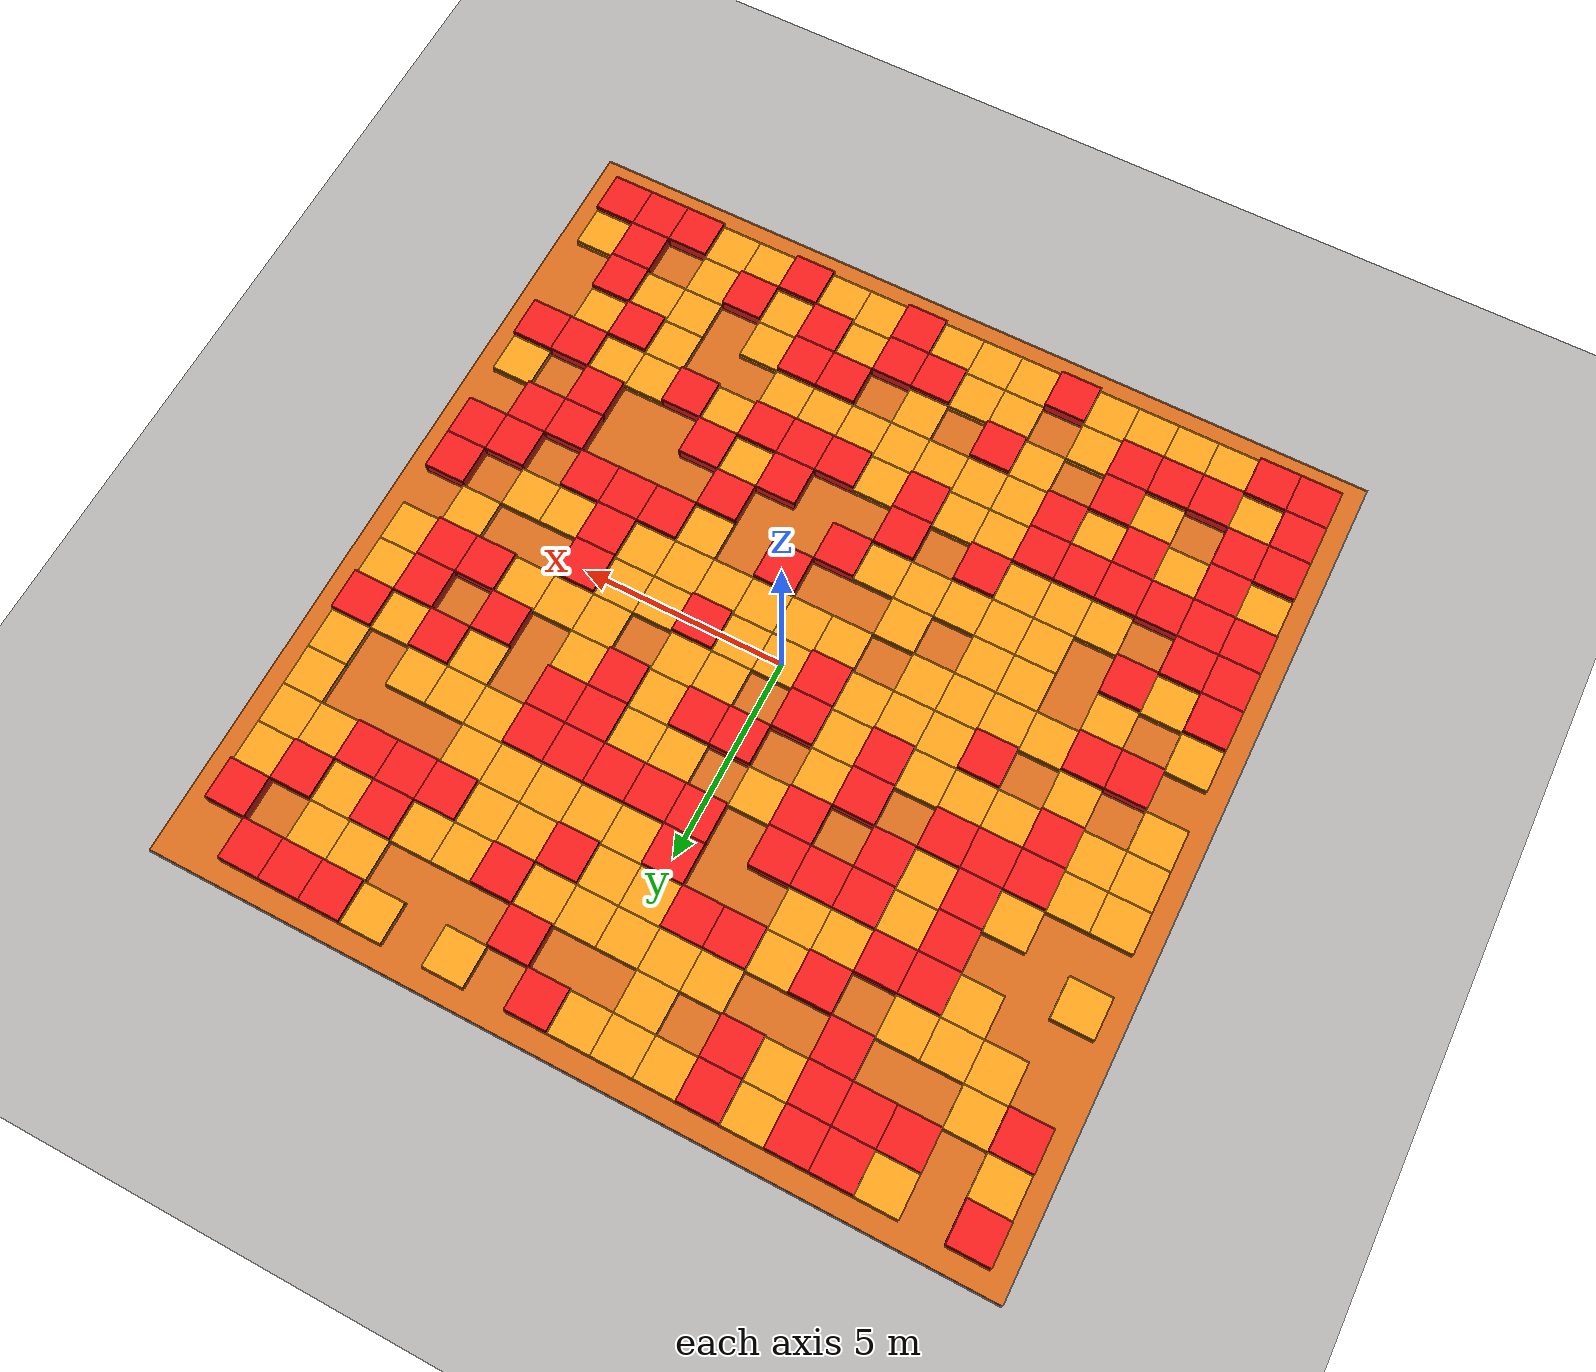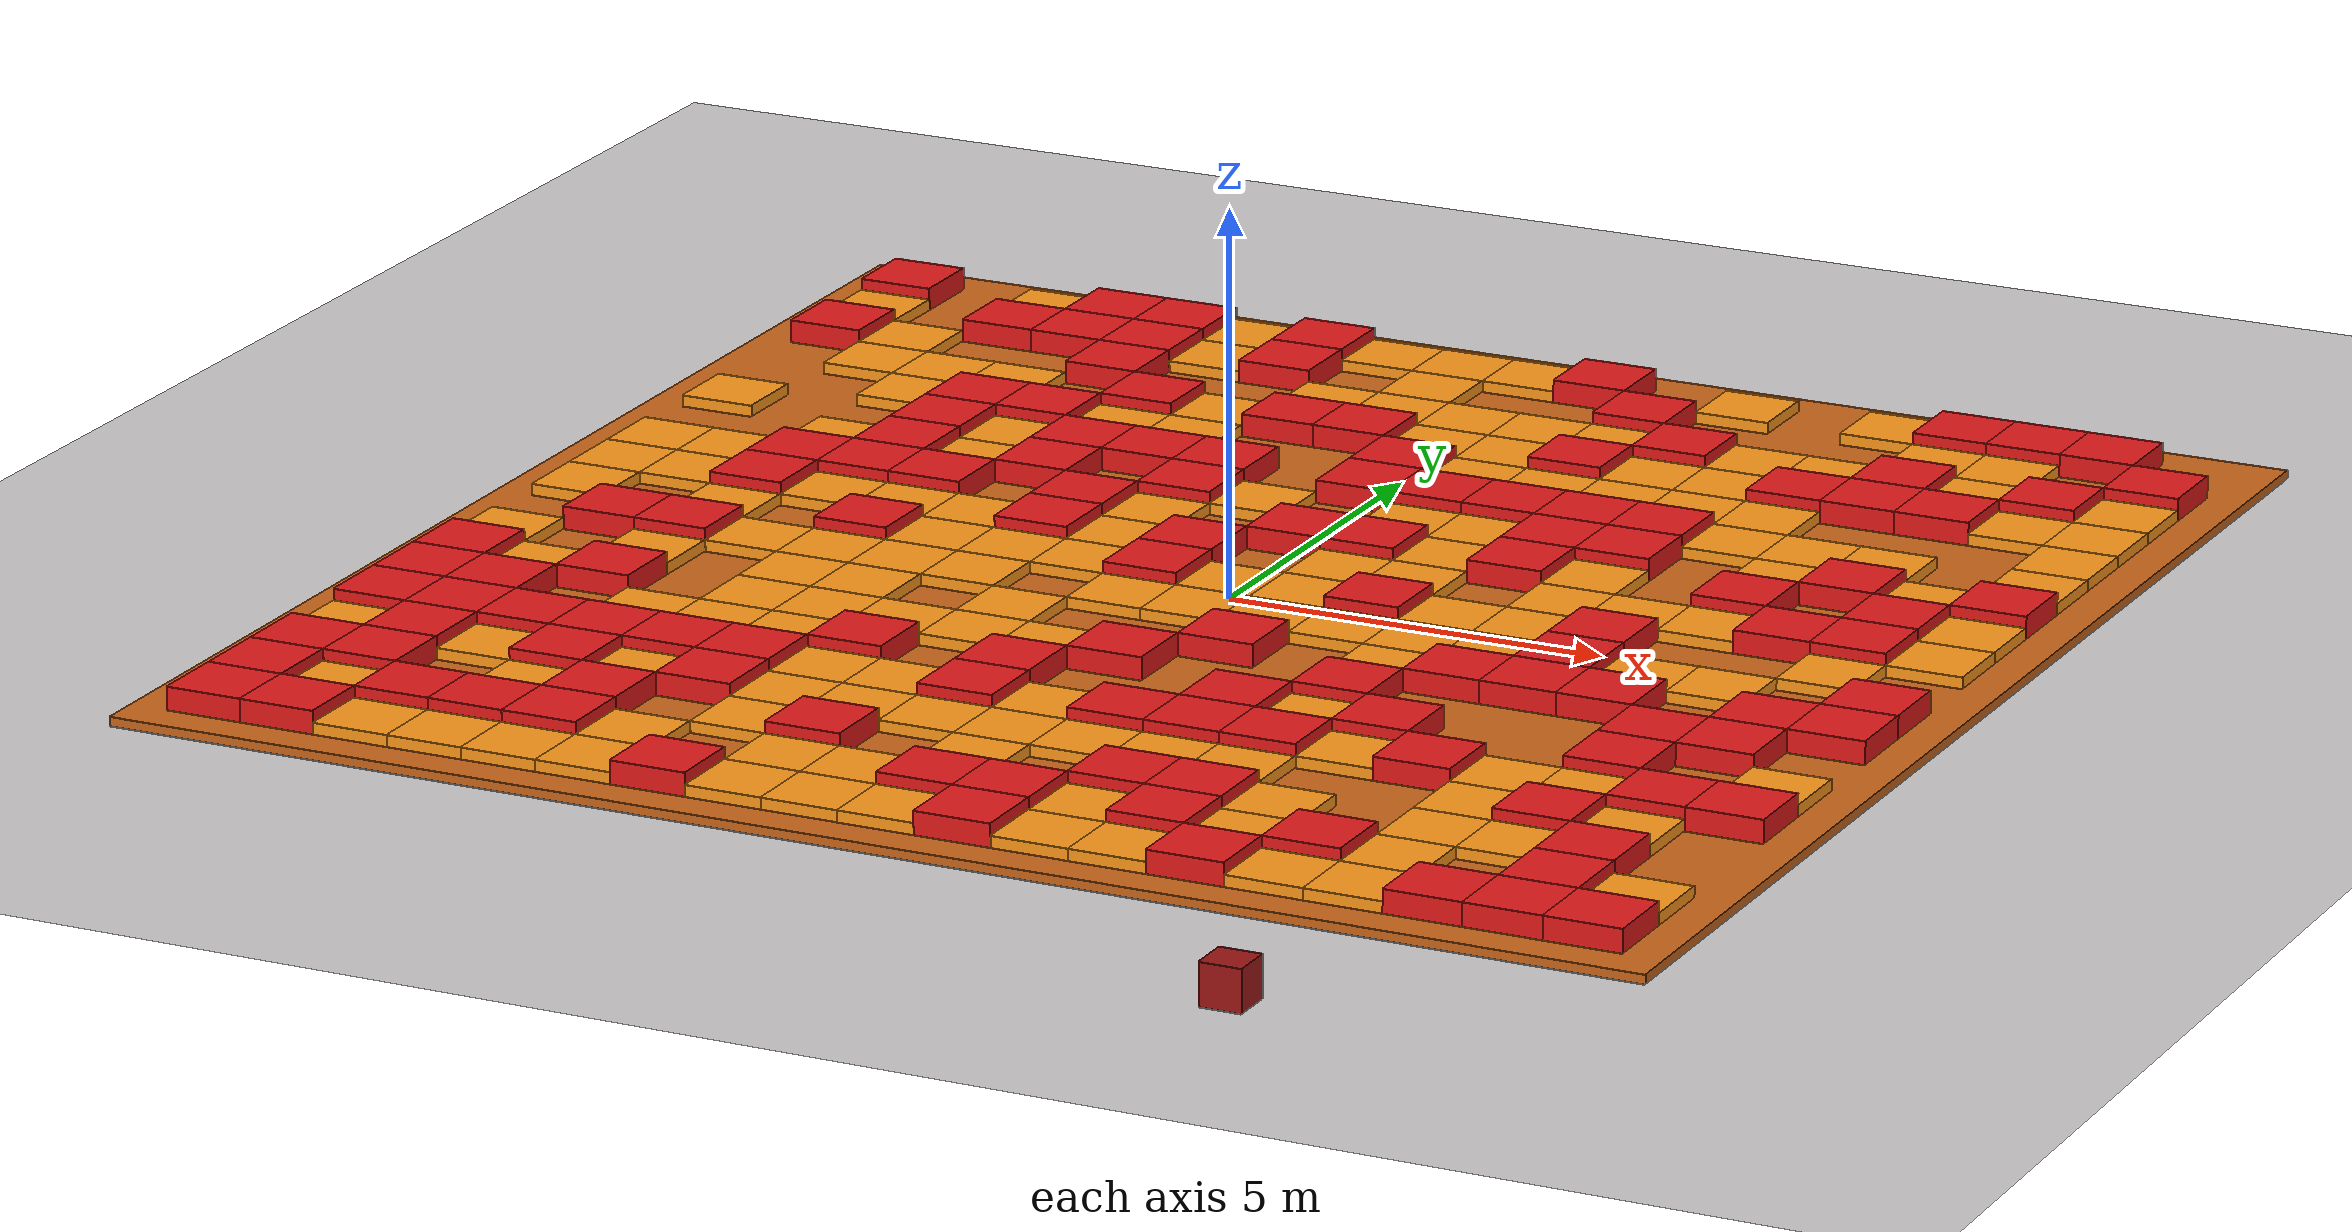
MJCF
<?xml version='1.0' encoding='utf-8'?>
<mujoco model="track_steps1m">
  <compiler angle="radian" />
  <asset>
    <texture type="skybox" builtin="gradient" rgb1="0.4 0.6 0.8" rgb2="0 0 0" width="512" height="512" />
    <texture name="tex_piso" type="2d" builtin="checker" rgb1="0.15 0.1 0.1" rgb2="0.08 0.05 0.05" width="512" height="512" />
    <material name="mat_piso" texture="tex_piso" texrepeat="20 20" texuniform="true" reflectance="0.1" />
    <texture name="tex_plataforma" type="2d" builtin="flat" rgb1="0.8 0.4 0.1" rgb2="0.1 0.15 0.2" width="512" height="512" />
    <material name="mat_plataforma" texture="tex_plataforma" texrepeat="40 40" texuniform="true" reflectance="0.1" />
  </asset>
  <worldbody>
    <light directional="true" pos="0 0 10" dir="0 0 -1" />
    <geom name="suelo" type="plane" size="40 40 0.1" material="mat_piso" condim="3" friction="1 0.005 0.0001" />
    <geom name="plataforma_gigante" type="box" size="10.0 10.0 0.06" pos="0 0 0.06" material="mat_plataforma" condim="3" friction="1 0.005 0.0001" />
    <geom name="virtual_obstacle" type="box" size="0.3 0.3 0.3" pos="0 0 -5" rgba="0.85 0.1 0.1 1" condim="3" friction="1 0.005 0.0001" />
    <geom name="step1m_0_0" type="box" size="0.5000 0.5000 0.1500" pos="-9.0000 -9.0000 0.2700" rgba="0.9 0.1 0.1 1" condim="3" friction="1 0.005 0.0001" />
    <geom name="step1m_0_1" type="box" size="0.5000 0.5000 0.1500" pos="-8.0000 -9.0000 0.2700" rgba="0.9 0.1 0.1 1" condim="3" friction="1 0.005 0.0001" />
    <geom name="step1m_0_2" type="box" size="0.5000 0.5000 0.0750" pos="-7.0000 -9.0000 0.1950" rgba="1 0.6 0.1 1" condim="3" friction="1 0.005 0.0001" />
    <geom name="step1m_0_3" type="box" size="0.5000 0.5000 0.0750" pos="-6.0000 -9.0000 0.1950" rgba="1 0.6 0.1 1" condim="3" friction="1 0.005 0.0001" />
    <geom name="step1m_0_4" type="box" size="0.5000 0.5000 0.0750" pos="-5.0000 -9.0000 0.1950" rgba="1 0.6 0.1 1" condim="3" friction="1 0.005 0.0001" />
    <geom name="step1m_0_5" type="box" size="0.5000 0.5000 0.0750" pos="-4.0000 -9.0000 0.1950" rgba="1 0.6 0.1 1" condim="3" friction="1 0.005 0.0001" />
    <geom name="step1m_0_6" type="box" size="0.5000 0.5000 0.1500" pos="-3.0000 -9.0000 0.2700" rgba="0.9 0.1 0.1 1" condim="3" friction="1 0.005 0.0001" />
    <geom name="step1m_0_7" type="box" size="0.5000 0.5000 0.0750" pos="-2.0000 -9.0000 0.1950" rgba="1 0.6 0.1 1" condim="3" friction="1 0.005 0.0001" />
    <geom name="step1m_0_8" type="box" size="0.5000 0.5000 0.0750" pos="-1.0000 -9.0000 0.1950" rgba="1 0.6 0.1 1" condim="3" friction="1 0.005 0.0001" />
    <geom name="step1m_0_9" type="box" size="0.5000 0.5000 0.0750" pos="0.0000 -9.0000 0.1950" rgba="1 0.6 0.1 1" condim="3" friction="1 0.005 0.0001" />
    <geom name="step1m_0_10" type="box" size="0.5000 0.5000 0.1500" pos="1.0000 -9.0000 0.2700" rgba="0.9 0.1 0.1 1" condim="3" friction="1 0.005 0.0001" />
    <geom name="step1m_0_11" type="box" size="0.5000 0.5000 0.0750" pos="2.0000 -9.0000 0.1950" rgba="1 0.6 0.1 1" condim="3" friction="1 0.005 0.0001" />
    <geom name="step1m_0_12" type="box" size="0.5000 0.5000 0.0750" pos="3.0000 -9.0000 0.1950" rgba="1 0.6 0.1 1" condim="3" friction="1 0.005 0.0001" />
    <geom name="step1m_0_13" type="box" size="0.5000 0.5000 0.1500" pos="4.0000 -9.0000 0.2700" rgba="0.9 0.1 0.1 1" condim="3" friction="1 0.005 0.0001" />
    <geom name="step1m_0_14" type="box" size="0.5000 0.5000 0.0750" pos="5.0000 -9.0000 0.1950" rgba="1 0.6 0.1 1" condim="3" friction="1 0.005 0.0001" />
    <geom name="step1m_0_15" type="box" size="0.5000 0.5000 0.0750" pos="6.0000 -9.0000 0.1950" rgba="1 0.6 0.1 1" condim="3" friction="1 0.005 0.0001" />
    <geom name="step1m_0_16" type="box" size="0.5000 0.5000 0.1500" pos="7.0000 -9.0000 0.2700" rgba="0.9 0.1 0.1 1" condim="3" friction="1 0.005 0.0001" />
    <geom name="step1m_0_17" type="box" size="0.5000 0.5000 0.1500" pos="8.0000 -9.0000 0.2700" rgba="0.9 0.1 0.1 1" condim="3" friction="1 0.005 0.0001" />
    <geom name="step1m_0_18" type="box" size="0.5000 0.5000 0.1500" pos="9.0000 -9.0000 0.2700" rgba="0.9 0.1 0.1 1" condim="3" friction="1 0.005 0.0001" />
    <geom name="step1m_1_0" type="box" size="0.5000 0.5000 0.1500" pos="-9.0000 -8.0000 0.2700" rgba="0.9 0.1 0.1 1" condim="3" friction="1 0.005 0.0001" />
    <geom name="step1m_1_1" type="box" size="0.5000 0.5000 0.0750" pos="-8.0000 -8.0000 0.1950" rgba="1 0.6 0.1 1" condim="3" friction="1 0.005 0.0001" />
    <geom name="step1m_1_2" type="box" size="0.5000 0.5000 0.1500" pos="-7.0000 -8.0000 0.2700" rgba="0.9 0.1 0.1 1" condim="3" friction="1 0.005 0.0001" />
    <geom name="step1m_1_3" type="box" size="0.5000 0.5000 0.1500" pos="-6.0000 -8.0000 0.2700" rgba="0.9 0.1 0.1 1" condim="3" friction="1 0.005 0.0001" />
    <geom name="step1m_1_4" type="box" size="0.5000 0.5000 0.1500" pos="-5.0000 -8.0000 0.2700" rgba="0.9 0.1 0.1 1" condim="3" friction="1 0.005 0.0001" />
    <geom name="step1m_1_5" type="box" size="0.5000 0.5000 0.0750" pos="-4.0000 -8.0000 0.1950" rgba="1 0.6 0.1 1" condim="3" friction="1 0.005 0.0001" />
    <geom name="step1m_1_7" type="box" size="0.5000 0.5000 0.0750" pos="-2.0000 -8.0000 0.1950" rgba="1 0.6 0.1 1" condim="3" friction="1 0.005 0.0001" />
    <geom name="step1m_1_8" type="box" size="0.5000 0.5000 0.0750" pos="-1.0000 -8.0000 0.1950" rgba="1 0.6 0.1 1" condim="3" friction="1 0.005 0.0001" />
    <geom name="step1m_1_9" type="box" size="0.5000 0.5000 0.1500" pos="0.0000 -8.0000 0.2700" rgba="0.9 0.1 0.1 1" condim="3" friction="1 0.005 0.0001" />
    <geom name="step1m_1_10" type="box" size="0.5000 0.5000 0.1500" pos="1.0000 -8.0000 0.2700" rgba="0.9 0.1 0.1 1" condim="3" friction="1 0.005 0.0001" />
    <geom name="step1m_1_11" type="box" size="0.5000 0.5000 0.0750" pos="2.0000 -8.0000 0.1950" rgba="1 0.6 0.1 1" condim="3" friction="1 0.005 0.0001" />
    <geom name="step1m_1_12" type="box" size="0.5000 0.5000 0.1500" pos="3.0000 -8.0000 0.2700" rgba="0.9 0.1 0.1 1" condim="3" friction="1 0.005 0.0001" />
    <geom name="step1m_1_13" type="box" size="0.5000 0.5000 0.0750" pos="4.0000 -8.0000 0.1950" rgba="1 0.6 0.1 1" condim="3" friction="1 0.005 0.0001" />
    <geom name="step1m_1_14" type="box" size="0.5000 0.5000 0.1500" pos="5.0000 -8.0000 0.2700" rgba="0.9 0.1 0.1 1" condim="3" friction="1 0.005 0.0001" />
    <geom name="step1m_1_15" type="box" size="0.5000 0.5000 0.0750" pos="6.0000 -8.0000 0.1950" rgba="1 0.6 0.1 1" condim="3" friction="1 0.005 0.0001" />
    <geom name="step1m_1_17" type="box" size="0.5000 0.5000 0.1500" pos="8.0000 -8.0000 0.2700" rgba="0.9 0.1 0.1 1" condim="3" friction="1 0.005 0.0001" />
    <geom name="step1m_1_18" type="box" size="0.5000 0.5000 0.0750" pos="9.0000 -8.0000 0.1950" rgba="1 0.6 0.1 1" condim="3" friction="1 0.005 0.0001" />
    <geom name="step1m_2_0" type="box" size="0.5000 0.5000 0.1500" pos="-9.0000 -7.0000 0.2700" rgba="0.9 0.1 0.1 1" condim="3" friction="1 0.005 0.0001" />
    <geom name="step1m_2_1" type="box" size="0.5000 0.5000 0.1500" pos="-8.0000 -7.0000 0.2700" rgba="0.9 0.1 0.1 1" condim="3" friction="1 0.005 0.0001" />
    <geom name="step1m_2_3" type="box" size="0.5000 0.5000 0.0750" pos="-6.0000 -7.0000 0.1950" rgba="1 0.6 0.1 1" condim="3" friction="1 0.005 0.0001" />
    <geom name="step1m_2_4" type="box" size="0.5000 0.5000 0.1500" pos="-5.0000 -7.0000 0.2700" rgba="0.9 0.1 0.1 1" condim="3" friction="1 0.005 0.0001" />
    <geom name="step1m_2_6" type="box" size="0.5000 0.5000 0.0750" pos="-3.0000 -7.0000 0.1950" rgba="1 0.6 0.1 1" condim="3" friction="1 0.005 0.0001" />
    <geom name="step1m_2_7" type="box" size="0.5000 0.5000 0.1500" pos="-2.0000 -7.0000 0.2700" rgba="0.9 0.1 0.1 1" condim="3" friction="1 0.005 0.0001" />
    <geom name="step1m_2_9" type="box" size="0.5000 0.5000 0.0750" pos="0.0000 -7.0000 0.1950" rgba="1 0.6 0.1 1" condim="3" friction="1 0.005 0.0001" />
    <geom name="step1m_2_11" type="box" size="0.5000 0.5000 0.1500" pos="2.0000 -7.0000 0.2700" rgba="0.9 0.1 0.1 1" condim="3" friction="1 0.005 0.0001" />
    <geom name="step1m_2_12" type="box" size="0.5000 0.5000 0.1500" pos="3.0000 -7.0000 0.2700" rgba="0.9 0.1 0.1 1" condim="3" friction="1 0.005 0.0001" />
    <geom name="step1m_2_13" type="box" size="0.5000 0.5000 0.0750" pos="4.0000 -7.0000 0.1950" rgba="1 0.6 0.1 1" condim="3" friction="1 0.005 0.0001" />
    <geom name="step1m_2_15" type="box" size="0.5000 0.5000 0.0750" pos="6.0000 -7.0000 0.1950" rgba="1 0.6 0.1 1" condim="3" friction="1 0.005 0.0001" />
    <geom name="step1m_2_16" type="box" size="0.5000 0.5000 0.0750" pos="7.0000 -7.0000 0.1950" rgba="1 0.6 0.1 1" condim="3" friction="1 0.005 0.0001" />
    <geom name="step1m_2_17" type="box" size="0.5000 0.5000 0.1500" pos="8.0000 -7.0000 0.2700" rgba="0.9 0.1 0.1 1" condim="3" friction="1 0.005 0.0001" />
    <geom name="step1m_3_0" type="box" size="0.5000 0.5000 0.0750" pos="-9.0000 -6.0000 0.1950" rgba="1 0.6 0.1 1" condim="3" friction="1 0.005 0.0001" />
    <geom name="step1m_3_1" type="box" size="0.5000 0.5000 0.1500" pos="-8.0000 -6.0000 0.2700" rgba="0.9 0.1 0.1 1" condim="3" friction="1 0.005 0.0001" />
    <geom name="step1m_3_2" type="box" size="0.5000 0.5000 0.0750" pos="-7.0000 -6.0000 0.1950" rgba="1 0.6 0.1 1" condim="3" friction="1 0.005 0.0001" />
    <geom name="step1m_3_3" type="box" size="0.5000 0.5000 0.1500" pos="-6.0000 -6.0000 0.2700" rgba="0.9 0.1 0.1 1" condim="3" friction="1 0.005 0.0001" />
    <geom name="step1m_3_4" type="box" size="0.5000 0.5000 0.0750" pos="-5.0000 -6.0000 0.1950" rgba="1 0.6 0.1 1" condim="3" friction="1 0.005 0.0001" />
    <geom name="step1m_3_5" type="box" size="0.5000 0.5000 0.1500" pos="-4.0000 -6.0000 0.2700" rgba="0.9 0.1 0.1 1" condim="3" friction="1 0.005 0.0001" />
    <geom name="step1m_3_6" type="box" size="0.5000 0.5000 0.0750" pos="-3.0000 -6.0000 0.1950" rgba="1 0.6 0.1 1" condim="3" friction="1 0.005 0.0001" />
    <geom name="step1m_3_7" type="box" size="0.5000 0.5000 0.0750" pos="-2.0000 -6.0000 0.1950" rgba="1 0.6 0.1 1" condim="3" friction="1 0.005 0.0001" />
    <geom name="step1m_3_8" type="box" size="0.5000 0.5000 0.0750" pos="-1.0000 -6.0000 0.1950" rgba="1 0.6 0.1 1" condim="3" friction="1 0.005 0.0001" />
    <geom name="step1m_3_9" type="box" size="0.5000 0.5000 0.0750" pos="0.0000 -6.0000 0.1950" rgba="1 0.6 0.1 1" condim="3" friction="1 0.005 0.0001" />
    <geom name="step1m_3_10" type="box" size="0.5000 0.5000 0.0750" pos="1.0000 -6.0000 0.1950" rgba="1 0.6 0.1 1" condim="3" friction="1 0.005 0.0001" />
    <geom name="step1m_3_11" type="box" size="0.5000 0.5000 0.0750" pos="2.0000 -6.0000 0.1950" rgba="1 0.6 0.1 1" condim="3" friction="1 0.005 0.0001" />
    <geom name="step1m_3_12" type="box" size="0.5000 0.5000 0.0750" pos="3.0000 -6.0000 0.1950" rgba="1 0.6 0.1 1" condim="3" friction="1 0.005 0.0001" />
    <geom name="step1m_3_15" type="box" size="0.5000 0.5000 0.0750" pos="6.0000 -6.0000 0.1950" rgba="1 0.6 0.1 1" condim="3" friction="1 0.005 0.0001" />
    <geom name="step1m_3_16" type="box" size="0.5000 0.5000 0.1500" pos="7.0000 -6.0000 0.2700" rgba="0.9 0.1 0.1 1" condim="3" friction="1 0.005 0.0001" />
    <geom name="step1m_3_17" type="box" size="0.5000 0.5000 0.0750" pos="8.0000 -6.0000 0.1950" rgba="1 0.6 0.1 1" condim="3" friction="1 0.005 0.0001" />
    <geom name="step1m_4_0" type="box" size="0.5000 0.5000 0.1500" pos="-9.0000 -5.0000 0.2700" rgba="0.9 0.1 0.1 1" condim="3" friction="1 0.005 0.0001" />
    <geom name="step1m_4_1" type="box" size="0.5000 0.5000 0.1500" pos="-8.0000 -5.0000 0.2700" rgba="0.9 0.1 0.1 1" condim="3" friction="1 0.005 0.0001" />
    <geom name="step1m_4_2" type="box" size="0.5000 0.5000 0.1500" pos="-7.0000 -5.0000 0.2700" rgba="0.9 0.1 0.1 1" condim="3" friction="1 0.005 0.0001" />
    <geom name="step1m_4_3" type="box" size="0.5000 0.5000 0.1500" pos="-6.0000 -5.0000 0.2700" rgba="0.9 0.1 0.1 1" condim="3" friction="1 0.005 0.0001" />
    <geom name="step1m_4_4" type="box" size="0.5000 0.5000 0.1500" pos="-5.0000 -5.0000 0.2700" rgba="0.9 0.1 0.1 1" condim="3" friction="1 0.005 0.0001" />
    <geom name="step1m_4_5" type="box" size="0.5000 0.5000 0.1500" pos="-4.0000 -5.0000 0.2700" rgba="0.9 0.1 0.1 1" condim="3" friction="1 0.005 0.0001" />
    <geom name="step1m_4_6" type="box" size="0.5000 0.5000 0.0750" pos="-3.0000 -5.0000 0.1950" rgba="1 0.6 0.1 1" condim="3" friction="1 0.005 0.0001" />
    <geom name="step1m_4_7" type="box" size="0.5000 0.5000 0.0750" pos="-2.0000 -5.0000 0.1950" rgba="1 0.6 0.1 1" condim="3" friction="1 0.005 0.0001" />
    <geom name="step1m_4_8" type="box" size="0.5000 0.5000 0.1500" pos="-1.0000 -5.0000 0.2700" rgba="0.9 0.1 0.1 1" condim="3" friction="1 0.005 0.0001" />
    <geom name="step1m_4_9" type="box" size="0.5000 0.5000 0.0750" pos="0.0000 -5.0000 0.1950" rgba="1 0.6 0.1 1" condim="3" friction="1 0.005 0.0001" />
    <geom name="step1m_4_10" type="box" size="0.5000 0.5000 0.1500" pos="1.0000 -5.0000 0.2700" rgba="0.9 0.1 0.1 1" condim="3" friction="1 0.005 0.0001" />
    <geom name="step1m_4_11" type="box" size="0.5000 0.5000 0.1500" pos="2.0000 -5.0000 0.2700" rgba="0.9 0.1 0.1 1" condim="3" friction="1 0.005 0.0001" />
    <geom name="step1m_4_12" type="box" size="0.5000 0.5000 0.1500" pos="3.0000 -5.0000 0.2700" rgba="0.9 0.1 0.1 1" condim="3" friction="1 0.005 0.0001" />
    <geom name="step1m_4_13" type="box" size="0.5000 0.5000 0.0750" pos="4.0000 -5.0000 0.1950" rgba="1 0.6 0.1 1" condim="3" friction="1 0.005 0.0001" />
    <geom name="step1m_4_14" type="box" size="0.5000 0.5000 0.1500" pos="5.0000 -5.0000 0.2700" rgba="0.9 0.1 0.1 1" condim="3" friction="1 0.005 0.0001" />
    <geom name="step1m_4_15" type="box" size="0.5000 0.5000 0.0750" pos="6.0000 -5.0000 0.1950" rgba="1 0.6 0.1 1" condim="3" friction="1 0.005 0.0001" />
    <geom name="step1m_4_16" type="box" size="0.5000 0.5000 0.0750" pos="7.0000 -5.0000 0.1950" rgba="1 0.6 0.1 1" condim="3" friction="1 0.005 0.0001" />
    <geom name="step1m_4_17" type="box" size="0.5000 0.5000 0.1500" pos="8.0000 -5.0000 0.2700" rgba="0.9 0.1 0.1 1" condim="3" friction="1 0.005 0.0001" />
    <geom name="step1m_4_18" type="box" size="0.5000 0.5000 0.1500" pos="9.0000 -5.0000 0.2700" rgba="0.9 0.1 0.1 1" condim="3" friction="1 0.005 0.0001" />
    <geom name="step1m_5_0" type="box" size="0.5000 0.5000 0.1500" pos="-9.0000 -4.0000 0.2700" rgba="0.9 0.1 0.1 1" condim="3" friction="1 0.005 0.0001" />
    <geom name="step1m_5_1" type="box" size="0.5000 0.5000 0.1500" pos="-8.0000 -4.0000 0.2700" rgba="0.9 0.1 0.1 1" condim="3" friction="1 0.005 0.0001" />
    <geom name="step1m_5_3" type="box" size="0.5000 0.5000 0.0750" pos="-6.0000 -4.0000 0.1950" rgba="1 0.6 0.1 1" condim="3" friction="1 0.005 0.0001" />
    <geom name="step1m_5_4" type="box" size="0.5000 0.5000 0.0750" pos="-5.0000 -4.0000 0.1950" rgba="1 0.6 0.1 1" condim="3" friction="1 0.005 0.0001" />
    <geom name="step1m_5_5" type="box" size="0.5000 0.5000 0.0750" pos="-4.0000 -4.0000 0.1950" rgba="1 0.6 0.1 1" condim="3" friction="1 0.005 0.0001" />
    <geom name="step1m_5_6" type="box" size="0.5000 0.5000 0.1500" pos="-3.0000 -4.0000 0.2700" rgba="0.9 0.1 0.1 1" condim="3" friction="1 0.005 0.0001" />
    <geom name="step1m_5_8" type="box" size="0.5000 0.5000 0.1500" pos="-1.0000 -4.0000 0.2700" rgba="0.9 0.1 0.1 1" condim="3" friction="1 0.005 0.0001" />
    <geom name="step1m_5_11" type="box" size="0.5000 0.5000 0.1500" pos="2.0000 -4.0000 0.2700" rgba="0.9 0.1 0.1 1" condim="3" friction="1 0.005 0.0001" />
    <geom name="step1m_5_12" type="box" size="0.5000 0.5000 0.0750" pos="3.0000 -4.0000 0.1950" rgba="1 0.6 0.1 1" condim="3" friction="1 0.005 0.0001" />
    <geom name="step1m_5_13" type="box" size="0.5000 0.5000 0.1500" pos="4.0000 -4.0000 0.2700" rgba="0.9 0.1 0.1 1" condim="3" friction="1 0.005 0.0001" />
    <geom name="step1m_5_16" type="box" size="0.5000 0.5000 0.1500" pos="7.0000 -4.0000 0.2700" rgba="0.9 0.1 0.1 1" condim="3" friction="1 0.005 0.0001" />
    <geom name="step1m_5_18" type="box" size="0.5000 0.5000 0.0750" pos="9.0000 -4.0000 0.1950" rgba="1 0.6 0.1 1" condim="3" friction="1 0.005 0.0001" />
    <geom name="step1m_6_0" type="box" size="0.5000 0.5000 0.1500" pos="-9.0000 -3.0000 0.2700" rgba="0.9 0.1 0.1 1" condim="3" friction="1 0.005 0.0001" />
    <geom name="step1m_6_1" type="box" size="0.5000 0.5000 0.0750" pos="-8.0000 -3.0000 0.1950" rgba="1 0.6 0.1 1" condim="3" friction="1 0.005 0.0001" />
    <geom name="step1m_6_2" type="box" size="0.5000 0.5000 0.1500" pos="-7.0000 -3.0000 0.2700" rgba="0.9 0.1 0.1 1" condim="3" friction="1 0.005 0.0001" />
    <geom name="step1m_6_4" type="box" size="0.5000 0.5000 0.0750" pos="-5.0000 -3.0000 0.1950" rgba="1 0.6 0.1 1" condim="3" friction="1 0.005 0.0001" />
    <geom name="step1m_6_5" type="box" size="0.5000 0.5000 0.0750" pos="-4.0000 -3.0000 0.1950" rgba="1 0.6 0.1 1" condim="3" friction="1 0.005 0.0001" />
    <geom name="step1m_6_6" type="box" size="0.5000 0.5000 0.0750" pos="-3.0000 -3.0000 0.1950" rgba="1 0.6 0.1 1" condim="3" friction="1 0.005 0.0001" />
    <geom name="step1m_6_7" type="box" size="0.5000 0.5000 0.0750" pos="-2.0000 -3.0000 0.1950" rgba="1 0.6 0.1 1" condim="3" friction="1 0.005 0.0001" />
    <geom name="step1m_6_8" type="box" size="0.5000 0.5000 0.0750" pos="-1.0000 -3.0000 0.1950" rgba="1 0.6 0.1 1" condim="3" friction="1 0.005 0.0001" />
    <geom name="step1m_6_9" type="box" size="0.5000 0.5000 0.1500" pos="0.0000 -3.0000 0.2700" rgba="0.9 0.1 0.1 1" condim="3" friction="1 0.005 0.0001" />
    <geom name="step1m_6_12" type="box" size="0.5000 0.5000 0.1500" pos="3.0000 -3.0000 0.2700" rgba="0.9 0.1 0.1 1" condim="3" friction="1 0.005 0.0001" />
    <geom name="step1m_6_16" type="box" size="0.5000 0.5000 0.1500" pos="7.0000 -3.0000 0.2700" rgba="0.9 0.1 0.1 1" condim="3" friction="1 0.005 0.0001" />
    <geom name="step1m_6_17" type="box" size="0.5000 0.5000 0.1500" pos="8.0000 -3.0000 0.2700" rgba="0.9 0.1 0.1 1" condim="3" friction="1 0.005 0.0001" />
    <geom name="step1m_7_0" type="box" size="0.5000 0.5000 0.0750" pos="-9.0000 -2.0000 0.1950" rgba="1 0.6 0.1 1" condim="3" friction="1 0.005 0.0001" />
    <geom name="step1m_7_2" type="box" size="0.5000 0.5000 0.0750" pos="-7.0000 -2.0000 0.1950" rgba="1 0.6 0.1 1" condim="3" friction="1 0.005 0.0001" />
    <geom name="step1m_7_4" type="box" size="0.5000 0.5000 0.0750" pos="-5.0000 -2.0000 0.1950" rgba="1 0.6 0.1 1" condim="3" friction="1 0.005 0.0001" />
    <geom name="step1m_7_5" type="box" size="0.5000 0.5000 0.0750" pos="-4.0000 -2.0000 0.1950" rgba="1 0.6 0.1 1" condim="3" friction="1 0.005 0.0001" />
    <geom name="step1m_7_7" type="box" size="0.5000 0.5000 0.0750" pos="-2.0000 -2.0000 0.1950" rgba="1 0.6 0.1 1" condim="3" friction="1 0.005 0.0001" />
    <geom name="step1m_7_10" type="box" size="0.5000 0.5000 0.1500" pos="1.0000 -2.0000 0.2700" rgba="0.9 0.1 0.1 1" condim="3" friction="1 0.005 0.0001" />
    <geom name="step1m_7_12" type="box" size="0.5000 0.5000 0.0750" pos="3.0000 -2.0000 0.1950" rgba="1 0.6 0.1 1" condim="3" friction="1 0.005 0.0001" />
    <geom name="step1m_7_13" type="box" size="0.5000 0.5000 0.1500" pos="4.0000 -2.0000 0.2700" rgba="0.9 0.1 0.1 1" condim="3" friction="1 0.005 0.0001" />
    <geom name="step1m_7_14" type="box" size="0.5000 0.5000 0.1500" pos="5.0000 -2.0000 0.2700" rgba="0.9 0.1 0.1 1" condim="3" friction="1 0.005 0.0001" />
    <geom name="step1m_7_15" type="box" size="0.5000 0.5000 0.1500" pos="6.0000 -2.0000 0.2700" rgba="0.9 0.1 0.1 1" condim="3" friction="1 0.005 0.0001" />
    <geom name="step1m_7_17" type="box" size="0.5000 0.5000 0.1500" pos="8.0000 -2.0000 0.2700" rgba="0.9 0.1 0.1 1" condim="3" friction="1 0.005 0.0001" />
    <geom name="step1m_7_18" type="box" size="0.5000 0.5000 0.1500" pos="9.0000 -2.0000 0.2700" rgba="0.9 0.1 0.1 1" condim="3" friction="1 0.005 0.0001" />
    <geom name="step1m_8_1" type="box" size="0.5000 0.5000 0.1500" pos="-8.0000 -1.0000 0.2700" rgba="0.9 0.1 0.1 1" condim="3" friction="1 0.005 0.0001" />
    <geom name="step1m_8_2" type="box" size="0.5000 0.5000 0.1500" pos="-7.0000 -1.0000 0.2700" rgba="0.9 0.1 0.1 1" condim="3" friction="1 0.005 0.0001" />
    <geom name="step1m_8_3" type="box" size="0.5000 0.5000 0.0750" pos="-6.0000 -1.0000 0.1950" rgba="1 0.6 0.1 1" condim="3" friction="1 0.005 0.0001" />
    <geom name="step1m_8_4" type="box" size="0.5000 0.5000 0.0750" pos="-5.0000 -1.0000 0.1950" rgba="1 0.6 0.1 1" condim="3" friction="1 0.005 0.0001" />
    <geom name="step1m_8_5" type="box" size="0.5000 0.5000 0.0750" pos="-4.0000 -1.0000 0.1950" rgba="1 0.6 0.1 1" condim="3" friction="1 0.005 0.0001" />
    <geom name="step1m_8_6" type="box" size="0.5000 0.5000 0.0750" pos="-3.0000 -1.0000 0.1950" rgba="1 0.6 0.1 1" condim="3" friction="1 0.005 0.0001" />
    <geom name="step1m_8_8" type="box" size="0.5000 0.5000 0.0750" pos="-1.0000 -1.0000 0.1950" rgba="1 0.6 0.1 1" condim="3" friction="1 0.005 0.0001" />
    <geom name="step1m_8_9" type="box" size="0.5000 0.5000 0.0750" pos="0.0000 -1.0000 0.1950" rgba="1 0.6 0.1 1" condim="3" friction="1 0.005 0.0001" />
    <geom name="step1m_8_10" type="box" size="0.5000 0.5000 0.0750" pos="1.0000 -1.0000 0.1950" rgba="1 0.6 0.1 1" condim="3" friction="1 0.005 0.0001" />
    <geom name="step1m_8_11" type="box" size="0.5000 0.5000 0.0750" pos="2.0000 -1.0000 0.1950" rgba="1 0.6 0.1 1" condim="3" friction="1 0.005 0.0001" />
    <geom name="step1m_8_12" type="box" size="0.5000 0.5000 0.0750" pos="3.0000 -1.0000 0.1950" rgba="1 0.6 0.1 1" condim="3" friction="1 0.005 0.0001" />
    <geom name="step1m_8_13" type="box" size="0.5000 0.5000 0.0750" pos="4.0000 -1.0000 0.1950" rgba="1 0.6 0.1 1" condim="3" friction="1 0.005 0.0001" />
    <geom name="step1m_8_14" type="box" size="0.5000 0.5000 0.1500" pos="5.0000 -1.0000 0.2700" rgba="0.9 0.1 0.1 1" condim="3" friction="1 0.005 0.0001" />
    <geom name="step1m_8_15" type="box" size="0.5000 0.5000 0.0750" pos="6.0000 -1.0000 0.1950" rgba="1 0.6 0.1 1" condim="3" friction="1 0.005 0.0001" />
    <geom name="step1m_8_16" type="box" size="0.5000 0.5000 0.0750" pos="7.0000 -1.0000 0.1950" rgba="1 0.6 0.1 1" condim="3" friction="1 0.005 0.0001" />
    <geom name="step1m_8_18" type="box" size="0.5000 0.5000 0.1500" pos="9.0000 -1.0000 0.2700" rgba="0.9 0.1 0.1 1" condim="3" friction="1 0.005 0.0001" />
    <geom name="step1m_9_0" type="box" size="0.5000 0.5000 0.0750" pos="-9.0000 0.0000 0.1950" rgba="1 0.6 0.1 1" condim="3" friction="1 0.005 0.0001" />
    <geom name="step1m_9_2" type="box" size="0.5000 0.5000 0.0750" pos="-7.0000 0.0000 0.1950" rgba="1 0.6 0.1 1" condim="3" friction="1 0.005 0.0001" />
    <geom name="step1m_9_4" type="box" size="0.5000 0.5000 0.1500" pos="-5.0000 0.0000 0.2700" rgba="0.9 0.1 0.1 1" condim="3" friction="1 0.005 0.0001" />
    <geom name="step1m_9_5" type="box" size="0.5000 0.5000 0.0750" pos="-4.0000 0.0000 0.1950" rgba="1 0.6 0.1 1" condim="3" friction="1 0.005 0.0001" />
    <geom name="step1m_9_6" type="box" size="0.5000 0.5000 0.0750" pos="-3.0000 0.0000 0.1950" rgba="1 0.6 0.1 1" condim="3" friction="1 0.005 0.0001" />
    <geom name="step1m_9_7" type="box" size="0.5000 0.5000 0.0750" pos="-2.0000 0.0000 0.1950" rgba="1 0.6 0.1 1" condim="3" friction="1 0.005 0.0001" />
    <geom name="step1m_9_8" type="box" size="0.5000 0.5000 0.1500" pos="-1.0000 0.0000 0.2700" rgba="0.9 0.1 0.1 1" condim="3" friction="1 0.005 0.0001" />
    <geom name="step1m_9_9" type="box" size="0.5000 0.5000 0.0750" pos="0.0000 0.0000 0.1950" rgba="1 0.6 0.1 1" condim="3" friction="1 0.005 0.0001" />
    <geom name="step1m_9_10" type="box" size="0.5000 0.5000 0.0750" pos="1.0000 0.0000 0.1950" rgba="1 0.6 0.1 1" condim="3" friction="1 0.005 0.0001" />
    <geom name="step1m_9_11" type="box" size="0.5000 0.5000 0.1500" pos="2.0000 0.0000 0.2700" rgba="0.9 0.1 0.1 1" condim="3" friction="1 0.005 0.0001" />
    <geom name="step1m_9_12" type="box" size="0.5000 0.5000 0.0750" pos="3.0000 0.0000 0.1950" rgba="1 0.6 0.1 1" condim="3" friction="1 0.005 0.0001" />
    <geom name="step1m_9_13" type="box" size="0.5000 0.5000 0.0750" pos="4.0000 0.0000 0.1950" rgba="1 0.6 0.1 1" condim="3" friction="1 0.005 0.0001" />
    <geom name="step1m_9_14" type="box" size="0.5000 0.5000 0.1500" pos="5.0000 0.0000 0.2700" rgba="0.9 0.1 0.1 1" condim="3" friction="1 0.005 0.0001" />
    <geom name="step1m_9_17" type="box" size="0.5000 0.5000 0.0750" pos="8.0000 0.0000 0.1950" rgba="1 0.6 0.1 1" condim="3" friction="1 0.005 0.0001" />
    <geom name="step1m_10_0" type="box" size="0.5000 0.5000 0.0750" pos="-9.0000 1.0000 0.1950" rgba="1 0.6 0.1 1" condim="3" friction="1 0.005 0.0001" />
    <geom name="step1m_10_1" type="box" size="0.5000 0.5000 0.0750" pos="-8.0000 1.0000 0.1950" rgba="1 0.6 0.1 1" condim="3" friction="1 0.005 0.0001" />
    <geom name="step1m_10_2" type="box" size="0.5000 0.5000 0.1500" pos="-7.0000 1.0000 0.2700" rgba="0.9 0.1 0.1 1" condim="3" friction="1 0.005 0.0001" />
    <geom name="step1m_10_3" type="box" size="0.5000 0.5000 0.0750" pos="-6.0000 1.0000 0.1950" rgba="1 0.6 0.1 1" condim="3" friction="1 0.005 0.0001" />
    <geom name="step1m_10_4" type="box" size="0.5000 0.5000 0.0750" pos="-5.0000 1.0000 0.1950" rgba="1 0.6 0.1 1" condim="3" friction="1 0.005 0.0001" />
    <geom name="step1m_10_5" type="box" size="0.5000 0.5000 0.0750" pos="-4.0000 1.0000 0.1950" rgba="1 0.6 0.1 1" condim="3" friction="1 0.005 0.0001" />
    <geom name="step1m_10_6" type="box" size="0.5000 0.5000 0.1500" pos="-3.0000 1.0000 0.2700" rgba="0.9 0.1 0.1 1" condim="3" friction="1 0.005 0.0001" />
    <geom name="step1m_10_7" type="box" size="0.5000 0.5000 0.0750" pos="-2.0000 1.0000 0.1950" rgba="1 0.6 0.1 1" condim="3" friction="1 0.005 0.0001" />
    <geom name="step1m_10_8" type="box" size="0.5000 0.5000 0.1500" pos="-1.0000 1.0000 0.2700" rgba="0.9 0.1 0.1 1" condim="3" friction="1 0.005 0.0001" />
    <geom name="step1m_10_10" type="box" size="0.5000 0.5000 0.0750" pos="1.0000 1.0000 0.1950" rgba="1 0.6 0.1 1" condim="3" friction="1 0.005 0.0001" />
    <geom name="step1m_10_11" type="box" size="0.5000 0.5000 0.0750" pos="2.0000 1.0000 0.1950" rgba="1 0.6 0.1 1" condim="3" friction="1 0.005 0.0001" />
    <geom name="step1m_10_13" type="box" size="0.5000 0.5000 0.0750" pos="4.0000 1.0000 0.1950" rgba="1 0.6 0.1 1" condim="3" friction="1 0.005 0.0001" />
    <geom name="step1m_10_14" type="box" size="0.5000 0.5000 0.0750" pos="5.0000 1.0000 0.1950" rgba="1 0.6 0.1 1" condim="3" friction="1 0.005 0.0001" />
    <geom name="step1m_10_15" type="box" size="0.5000 0.5000 0.0750" pos="6.0000 1.0000 0.1950" rgba="1 0.6 0.1 1" condim="3" friction="1 0.005 0.0001" />
    <geom name="step1m_10_16" type="box" size="0.5000 0.5000 0.1500" pos="7.0000 1.0000 0.2700" rgba="0.9 0.1 0.1 1" condim="3" friction="1 0.005 0.0001" />
    <geom name="step1m_10_17" type="box" size="0.5000 0.5000 0.1500" pos="8.0000 1.0000 0.2700" rgba="0.9 0.1 0.1 1" condim="3" friction="1 0.005 0.0001" />
    <geom name="step1m_10_18" type="box" size="0.5000 0.5000 0.0750" pos="9.0000 1.0000 0.1950" rgba="1 0.6 0.1 1" condim="3" friction="1 0.005 0.0001" />
    <geom name="step1m_11_0" type="box" size="0.5000 0.5000 0.0750" pos="-9.0000 2.0000 0.1950" rgba="1 0.6 0.1 1" condim="3" friction="1 0.005 0.0001" />
    <geom name="step1m_11_1" type="box" size="0.5000 0.5000 0.0750" pos="-8.0000 2.0000 0.1950" rgba="1 0.6 0.1 1" condim="3" friction="1 0.005 0.0001" />
    <geom name="step1m_11_2" type="box" size="0.5000 0.5000 0.1500" pos="-7.0000 2.0000 0.2700" rgba="0.9 0.1 0.1 1" condim="3" friction="1 0.005 0.0001" />
    <geom name="step1m_11_3" type="box" size="0.5000 0.5000 0.1500" pos="-6.0000 2.0000 0.2700" rgba="0.9 0.1 0.1 1" condim="3" friction="1 0.005 0.0001" />
    <geom name="step1m_11_4" type="box" size="0.5000 0.5000 0.1500" pos="-5.0000 2.0000 0.2700" rgba="0.9 0.1 0.1 1" condim="3" friction="1 0.005 0.0001" />
    <geom name="step1m_11_6" type="box" size="0.5000 0.5000 0.1500" pos="-3.0000 2.0000 0.2700" rgba="0.9 0.1 0.1 1" condim="3" friction="1 0.005 0.0001" />
    <geom name="step1m_11_7" type="box" size="0.5000 0.5000 0.0750" pos="-2.0000 2.0000 0.1950" rgba="1 0.6 0.1 1" condim="3" friction="1 0.005 0.0001" />
    <geom name="step1m_11_9" type="box" size="0.5000 0.5000 0.1500" pos="0.0000 2.0000 0.2700" rgba="0.9 0.1 0.1 1" condim="3" friction="1 0.005 0.0001" />
    <geom name="step1m_11_10" type="box" size="0.5000 0.5000 0.1500" pos="1.0000 2.0000 0.2700" rgba="0.9 0.1 0.1 1" condim="3" friction="1 0.005 0.0001" />
    <geom name="step1m_11_11" type="box" size="0.5000 0.5000 0.0750" pos="2.0000 2.0000 0.1950" rgba="1 0.6 0.1 1" condim="3" friction="1 0.005 0.0001" />
    <geom name="step1m_11_12" type="box" size="0.5000 0.5000 0.1500" pos="3.0000 2.0000 0.2700" rgba="0.9 0.1 0.1 1" condim="3" friction="1 0.005 0.0001" />
    <geom name="step1m_11_13" type="box" size="0.5000 0.5000 0.0750" pos="4.0000 2.0000 0.1950" rgba="1 0.6 0.1 1" condim="3" friction="1 0.005 0.0001" />
    <geom name="step1m_11_15" type="box" size="0.5000 0.5000 0.1500" pos="6.0000 2.0000 0.2700" rgba="0.9 0.1 0.1 1" condim="3" friction="1 0.005 0.0001" />
    <geom name="step1m_11_17" type="box" size="0.5000 0.5000 0.1500" pos="8.0000 2.0000 0.2700" rgba="0.9 0.1 0.1 1" condim="3" friction="1 0.005 0.0001" />
    <geom name="step1m_11_18" type="box" size="0.5000 0.5000 0.0750" pos="9.0000 2.0000 0.1950" rgba="1 0.6 0.1 1" condim="3" friction="1 0.005 0.0001" />
    <geom name="step1m_12_2" type="box" size="0.5000 0.5000 0.0750" pos="-7.0000 3.0000 0.1950" rgba="1 0.6 0.1 1" condim="3" friction="1 0.005 0.0001" />
    <geom name="step1m_12_3" type="box" size="0.5000 0.5000 0.1500" pos="-6.0000 3.0000 0.2700" rgba="0.9 0.1 0.1 1" condim="3" friction="1 0.005 0.0001" />
    <geom name="step1m_12_4" type="box" size="0.5000 0.5000 0.0750" pos="-5.0000 3.0000 0.1950" rgba="1 0.6 0.1 1" condim="3" friction="1 0.005 0.0001" />
    <geom name="step1m_12_5" type="box" size="0.5000 0.5000 0.1500" pos="-4.0000 3.0000 0.2700" rgba="0.9 0.1 0.1 1" condim="3" friction="1 0.005 0.0001" />
    <geom name="step1m_12_7" type="box" size="0.5000 0.5000 0.1500" pos="-2.0000 3.0000 0.2700" rgba="0.9 0.1 0.1 1" condim="3" friction="1 0.005 0.0001" />
    <geom name="step1m_12_8" type="box" size="0.5000 0.5000 0.0750" pos="-1.0000 3.0000 0.1950" rgba="1 0.6 0.1 1" condim="3" friction="1 0.005 0.0001" />
    <geom name="step1m_12_10" type="box" size="0.5000 0.5000 0.0750" pos="1.0000 3.0000 0.1950" rgba="1 0.6 0.1 1" condim="3" friction="1 0.005 0.0001" />
    <geom name="step1m_12_11" type="box" size="0.5000 0.5000 0.0750" pos="2.0000 3.0000 0.1950" rgba="1 0.6 0.1 1" condim="3" friction="1 0.005 0.0001" />
    <geom name="step1m_12_12" type="box" size="0.5000 0.5000 0.1500" pos="3.0000 3.0000 0.2700" rgba="0.9 0.1 0.1 1" condim="3" friction="1 0.005 0.0001" />
    <geom name="step1m_12_13" type="box" size="0.5000 0.5000 0.1500" pos="4.0000 3.0000 0.2700" rgba="0.9 0.1 0.1 1" condim="3" friction="1 0.005 0.0001" />
    <geom name="step1m_12_15" type="box" size="0.5000 0.5000 0.0750" pos="6.0000 3.0000 0.1950" rgba="1 0.6 0.1 1" condim="3" friction="1 0.005 0.0001" />
    <geom name="step1m_12_16" type="box" size="0.5000 0.5000 0.1500" pos="7.0000 3.0000 0.2700" rgba="0.9 0.1 0.1 1" condim="3" friction="1 0.005 0.0001" />
    <geom name="step1m_12_17" type="box" size="0.5000 0.5000 0.0750" pos="8.0000 3.0000 0.1950" rgba="1 0.6 0.1 1" condim="3" friction="1 0.005 0.0001" />
    <geom name="step1m_12_18" type="box" size="0.5000 0.5000 0.1500" pos="9.0000 3.0000 0.2700" rgba="0.9 0.1 0.1 1" condim="3" friction="1 0.005 0.0001" />
    <geom name="step1m_13_0" type="box" size="0.5000 0.5000 0.0750" pos="-9.0000 4.0000 0.1950" rgba="1 0.6 0.1 1" condim="3" friction="1 0.005 0.0001" />
    <geom name="step1m_13_3" type="box" size="0.5000 0.5000 0.1500" pos="-6.0000 4.0000 0.2700" rgba="0.9 0.1 0.1 1" condim="3" friction="1 0.005 0.0001" />
    <geom name="step1m_13_4" type="box" size="0.5000 0.5000 0.0750" pos="-5.0000 4.0000 0.1950" rgba="1 0.6 0.1 1" condim="3" friction="1 0.005 0.0001" />
    <geom name="step1m_13_5" type="box" size="0.5000 0.5000 0.1500" pos="-4.0000 4.0000 0.2700" rgba="0.9 0.1 0.1 1" condim="3" friction="1 0.005 0.0001" />
    <geom name="step1m_13_6" type="box" size="0.5000 0.5000 0.1500" pos="-3.0000 4.0000 0.2700" rgba="0.9 0.1 0.1 1" condim="3" friction="1 0.005 0.0001" />
    <geom name="step1m_13_7" type="box" size="0.5000 0.5000 0.1500" pos="-2.0000 4.0000 0.2700" rgba="0.9 0.1 0.1 1" condim="3" friction="1 0.005 0.0001" />
    <geom name="step1m_13_9" type="box" size="0.5000 0.5000 0.1500" pos="0.0000 4.0000 0.2700" rgba="0.9 0.1 0.1 1" condim="3" friction="1 0.005 0.0001" />
    <geom name="step1m_13_10" type="box" size="0.5000 0.5000 0.1500" pos="1.0000 4.0000 0.2700" rgba="0.9 0.1 0.1 1" condim="3" friction="1 0.005 0.0001" />
    <geom name="step1m_13_11" type="box" size="0.5000 0.5000 0.1500" pos="2.0000 4.0000 0.2700" rgba="0.9 0.1 0.1 1" condim="3" friction="1 0.005 0.0001" />
    <geom name="step1m_13_12" type="box" size="0.5000 0.5000 0.1500" pos="3.0000 4.0000 0.2700" rgba="0.9 0.1 0.1 1" condim="3" friction="1 0.005 0.0001" />
    <geom name="step1m_13_13" type="box" size="0.5000 0.5000 0.1500" pos="4.0000 4.0000 0.2700" rgba="0.9 0.1 0.1 1" condim="3" friction="1 0.005 0.0001" />
    <geom name="step1m_13_14" type="box" size="0.5000 0.5000 0.0750" pos="5.0000 4.0000 0.1950" rgba="1 0.6 0.1 1" condim="3" friction="1 0.005 0.0001" />
    <geom name="step1m_13_15" type="box" size="0.5000 0.5000 0.0750" pos="6.0000 4.0000 0.1950" rgba="1 0.6 0.1 1" condim="3" friction="1 0.005 0.0001" />
    <geom name="step1m_13_16" type="box" size="0.5000 0.5000 0.0750" pos="7.0000 4.0000 0.1950" rgba="1 0.6 0.1 1" condim="3" friction="1 0.005 0.0001" />
    <geom name="step1m_13_18" type="box" size="0.5000 0.5000 0.0750" pos="9.0000 4.0000 0.1950" rgba="1 0.6 0.1 1" condim="3" friction="1 0.005 0.0001" />
    <geom name="step1m_14_2" type="box" size="0.5000 0.5000 0.0750" pos="-7.0000 5.0000 0.1950" rgba="1 0.6 0.1 1" condim="3" friction="1 0.005 0.0001" />
    <geom name="step1m_14_3" type="box" size="0.5000 0.5000 0.1500" pos="-6.0000 5.0000 0.2700" rgba="0.9 0.1 0.1 1" condim="3" friction="1 0.005 0.0001" />
    <geom name="step1m_14_4" type="box" size="0.5000 0.5000 0.1500" pos="-5.0000 5.0000 0.2700" rgba="0.9 0.1 0.1 1" condim="3" friction="1 0.005 0.0001" />
    <geom name="step1m_14_5" type="box" size="0.5000 0.5000 0.0750" pos="-4.0000 5.0000 0.1950" rgba="1 0.6 0.1 1" condim="3" friction="1 0.005 0.0001" />
    <geom name="step1m_14_6" type="box" size="0.5000 0.5000 0.0750" pos="-3.0000 5.0000 0.1950" rgba="1 0.6 0.1 1" condim="3" friction="1 0.005 0.0001" />
    <geom name="step1m_14_9" type="box" size="0.5000 0.5000 0.1500" pos="0.0000 5.0000 0.2700" rgba="0.9 0.1 0.1 1" condim="3" friction="1 0.005 0.0001" />
    <geom name="step1m_14_10" type="box" size="0.5000 0.5000 0.0750" pos="1.0000 5.0000 0.1950" rgba="1 0.6 0.1 1" condim="3" friction="1 0.005 0.0001" />
    <geom name="step1m_14_11" type="box" size="0.5000 0.5000 0.0750" pos="2.0000 5.0000 0.1950" rgba="1 0.6 0.1 1" condim="3" friction="1 0.005 0.0001" />
    <geom name="step1m_14_12" type="box" size="0.5000 0.5000 0.0750" pos="3.0000 5.0000 0.1950" rgba="1 0.6 0.1 1" condim="3" friction="1 0.005 0.0001" />
    <geom name="step1m_14_13" type="box" size="0.5000 0.5000 0.0750" pos="4.0000 5.0000 0.1950" rgba="1 0.6 0.1 1" condim="3" friction="1 0.005 0.0001" />
    <geom name="step1m_14_14" type="box" size="0.5000 0.5000 0.0750" pos="5.0000 5.0000 0.1950" rgba="1 0.6 0.1 1" condim="3" friction="1 0.005 0.0001" />
    <geom name="step1m_14_18" type="box" size="0.5000 0.5000 0.0750" pos="9.0000 5.0000 0.1950" rgba="1 0.6 0.1 1" condim="3" friction="1 0.005 0.0001" />
    <geom name="step1m_15_1" type="box" size="0.5000 0.5000 0.0750" pos="-8.0000 6.0000 0.1950" rgba="1 0.6 0.1 1" condim="3" friction="1 0.005 0.0001" />
    <geom name="step1m_15_2" type="box" size="0.5000 0.5000 0.0750" pos="-7.0000 6.0000 0.1950" rgba="1 0.6 0.1 1" condim="3" friction="1 0.005 0.0001" />
    <geom name="step1m_15_3" type="box" size="0.5000 0.5000 0.0750" pos="-6.0000 6.0000 0.1950" rgba="1 0.6 0.1 1" condim="3" friction="1 0.005 0.0001" />
    <geom name="step1m_15_5" type="box" size="0.5000 0.5000 0.1500" pos="-4.0000 6.0000 0.2700" rgba="0.9 0.1 0.1 1" condim="3" friction="1 0.005 0.0001" />
    <geom name="step1m_15_6" type="box" size="0.5000 0.5000 0.0750" pos="-3.0000 6.0000 0.1950" rgba="1 0.6 0.1 1" condim="3" friction="1 0.005 0.0001" />
    <geom name="step1m_15_7" type="box" size="0.5000 0.5000 0.1500" pos="-2.0000 6.0000 0.2700" rgba="0.9 0.1 0.1 1" condim="3" friction="1 0.005 0.0001" />
    <geom name="step1m_15_8" type="box" size="0.5000 0.5000 0.1500" pos="-1.0000 6.0000 0.2700" rgba="0.9 0.1 0.1 1" condim="3" friction="1 0.005 0.0001" />
    <geom name="step1m_15_9" type="box" size="0.5000 0.5000 0.0750" pos="0.0000 6.0000 0.1950" rgba="1 0.6 0.1 1" condim="3" friction="1 0.005 0.0001" />
    <geom name="step1m_15_10" type="box" size="0.5000 0.5000 0.0750" pos="1.0000 6.0000 0.1950" rgba="1 0.6 0.1 1" condim="3" friction="1 0.005 0.0001" />
    <geom name="step1m_15_11" type="box" size="0.5000 0.5000 0.1500" pos="2.0000 6.0000 0.2700" rgba="0.9 0.1 0.1 1" condim="3" friction="1 0.005 0.0001" />
    <geom name="step1m_15_12" type="box" size="0.5000 0.5000 0.0750" pos="3.0000 6.0000 0.1950" rgba="1 0.6 0.1 1" condim="3" friction="1 0.005 0.0001" />
    <geom name="step1m_15_13" type="box" size="0.5000 0.5000 0.0750" pos="4.0000 6.0000 0.1950" rgba="1 0.6 0.1 1" condim="3" friction="1 0.005 0.0001" />
    <geom name="step1m_15_14" type="box" size="0.5000 0.5000 0.1500" pos="5.0000 6.0000 0.2700" rgba="0.9 0.1 0.1 1" condim="3" friction="1 0.005 0.0001" />
    <geom name="step1m_15_15" type="box" size="0.5000 0.5000 0.1500" pos="6.0000 6.0000 0.2700" rgba="0.9 0.1 0.1 1" condim="3" friction="1 0.005 0.0001" />
    <geom name="step1m_15_16" type="box" size="0.5000 0.5000 0.1500" pos="7.0000 6.0000 0.2700" rgba="0.9 0.1 0.1 1" condim="3" friction="1 0.005 0.0001" />
    <geom name="step1m_15_17" type="box" size="0.5000 0.5000 0.0750" pos="8.0000 6.0000 0.1950" rgba="1 0.6 0.1 1" condim="3" friction="1 0.005 0.0001" />
    <geom name="step1m_15_18" type="box" size="0.5000 0.5000 0.0750" pos="9.0000 6.0000 0.1950" rgba="1 0.6 0.1 1" condim="3" friction="1 0.005 0.0001" />
    <geom name="step1m_16_0" type="box" size="0.5000 0.5000 0.1500" pos="-9.0000 7.0000 0.2700" rgba="0.9 0.1 0.1 1" condim="3" friction="1 0.005 0.0001" />
    <geom name="step1m_16_1" type="box" size="0.5000 0.5000 0.0750" pos="-8.0000 7.0000 0.1950" rgba="1 0.6 0.1 1" condim="3" friction="1 0.005 0.0001" />
    <geom name="step1m_16_4" type="box" size="0.5000 0.5000 0.1500" pos="-5.0000 7.0000 0.2700" rgba="0.9 0.1 0.1 1" condim="3" friction="1 0.005 0.0001" />
    <geom name="step1m_16_7" type="box" size="0.5000 0.5000 0.0750" pos="-2.0000 7.0000 0.1950" rgba="1 0.6 0.1 1" condim="3" friction="1 0.005 0.0001" />
    <geom name="step1m_16_8" type="box" size="0.5000 0.5000 0.0750" pos="-1.0000 7.0000 0.1950" rgba="1 0.6 0.1 1" condim="3" friction="1 0.005 0.0001" />
    <geom name="step1m_16_9" type="box" size="0.5000 0.5000 0.0750" pos="0.0000 7.0000 0.1950" rgba="1 0.6 0.1 1" condim="3" friction="1 0.005 0.0001" />
    <geom name="step1m_16_10" type="box" size="0.5000 0.5000 0.0750" pos="1.0000 7.0000 0.1950" rgba="1 0.6 0.1 1" condim="3" friction="1 0.005 0.0001" />
    <geom name="step1m_16_11" type="box" size="0.5000 0.5000 0.0750" pos="2.0000 7.0000 0.1950" rgba="1 0.6 0.1 1" condim="3" friction="1 0.005 0.0001" />
    <geom name="step1m_16_12" type="box" size="0.5000 0.5000 0.1500" pos="3.0000 7.0000 0.2700" rgba="0.9 0.1 0.1 1" condim="3" friction="1 0.005 0.0001" />
    <geom name="step1m_16_13" type="box" size="0.5000 0.5000 0.0750" pos="4.0000 7.0000 0.1950" rgba="1 0.6 0.1 1" condim="3" friction="1 0.005 0.0001" />
    <geom name="step1m_16_14" type="box" size="0.5000 0.5000 0.0750" pos="5.0000 7.0000 0.1950" rgba="1 0.6 0.1 1" condim="3" friction="1 0.005 0.0001" />
    <geom name="step1m_16_15" type="box" size="0.5000 0.5000 0.1500" pos="6.0000 7.0000 0.2700" rgba="0.9 0.1 0.1 1" condim="3" friction="1 0.005 0.0001" />
    <geom name="step1m_16_16" type="box" size="0.5000 0.5000 0.0750" pos="7.0000 7.0000 0.1950" rgba="1 0.6 0.1 1" condim="3" friction="1 0.005 0.0001" />
    <geom name="step1m_16_17" type="box" size="0.5000 0.5000 0.1500" pos="8.0000 7.0000 0.2700" rgba="0.9 0.1 0.1 1" condim="3" friction="1 0.005 0.0001" />
    <geom name="step1m_16_18" type="box" size="0.5000 0.5000 0.0750" pos="9.0000 7.0000 0.1950" rgba="1 0.6 0.1 1" condim="3" friction="1 0.005 0.0001" />
    <geom name="step1m_17_0" type="box" size="0.5000 0.5000 0.0750" pos="-9.0000 8.0000 0.1950" rgba="1 0.6 0.1 1" condim="3" friction="1 0.005 0.0001" />
    <geom name="step1m_17_2" type="box" size="0.5000 0.5000 0.1500" pos="-7.0000 8.0000 0.2700" rgba="0.9 0.1 0.1 1" condim="3" friction="1 0.005 0.0001" />
    <geom name="step1m_17_3" type="box" size="0.5000 0.5000 0.1500" pos="-6.0000 8.0000 0.2700" rgba="0.9 0.1 0.1 1" condim="3" friction="1 0.005 0.0001" />
    <geom name="step1m_17_4" type="box" size="0.5000 0.5000 0.1500" pos="-5.0000 8.0000 0.2700" rgba="0.9 0.1 0.1 1" condim="3" friction="1 0.005 0.0001" />
    <geom name="step1m_17_5" type="box" size="0.5000 0.5000 0.0750" pos="-4.0000 8.0000 0.1950" rgba="1 0.6 0.1 1" condim="3" friction="1 0.005 0.0001" />
    <geom name="step1m_17_6" type="box" size="0.5000 0.5000 0.1500" pos="-3.0000 8.0000 0.2700" rgba="0.9 0.1 0.1 1" condim="3" friction="1 0.005 0.0001" />
    <geom name="step1m_17_8" type="box" size="0.5000 0.5000 0.0750" pos="-1.0000 8.0000 0.1950" rgba="1 0.6 0.1 1" condim="3" friction="1 0.005 0.0001" />
    <geom name="step1m_17_11" type="box" size="0.5000 0.5000 0.1500" pos="2.0000 8.0000 0.2700" rgba="0.9 0.1 0.1 1" condim="3" friction="1 0.005 0.0001" />
    <geom name="step1m_17_15" type="box" size="0.5000 0.5000 0.0750" pos="6.0000 8.0000 0.1950" rgba="1 0.6 0.1 1" condim="3" friction="1 0.005 0.0001" />
    <geom name="step1m_17_16" type="box" size="0.5000 0.5000 0.0750" pos="7.0000 8.0000 0.1950" rgba="1 0.6 0.1 1" condim="3" friction="1 0.005 0.0001" />
    <geom name="step1m_17_18" type="box" size="0.5000 0.5000 0.1500" pos="9.0000 8.0000 0.2700" rgba="0.9 0.1 0.1 1" condim="3" friction="1 0.005 0.0001" />
    <geom name="step1m_18_0" type="box" size="0.5000 0.5000 0.1500" pos="-9.0000 9.0000 0.2700" rgba="0.9 0.1 0.1 1" condim="3" friction="1 0.005 0.0001" />
    <geom name="step1m_18_2" type="box" size="0.5000 0.5000 0.0750" pos="-7.0000 9.0000 0.1950" rgba="1 0.6 0.1 1" condim="3" friction="1 0.005 0.0001" />
    <geom name="step1m_18_3" type="box" size="0.5000 0.5000 0.1500" pos="-6.0000 9.0000 0.2700" rgba="0.9 0.1 0.1 1" condim="3" friction="1 0.005 0.0001" />
    <geom name="step1m_18_4" type="box" size="0.5000 0.5000 0.1500" pos="-5.0000 9.0000 0.2700" rgba="0.9 0.1 0.1 1" condim="3" friction="1 0.005 0.0001" />
    <geom name="step1m_18_5" type="box" size="0.5000 0.5000 0.0750" pos="-4.0000 9.0000 0.1950" rgba="1 0.6 0.1 1" condim="3" friction="1 0.005 0.0001" />
    <geom name="step1m_18_6" type="box" size="0.5000 0.5000 0.1500" pos="-3.0000 9.0000 0.2700" rgba="0.9 0.1 0.1 1" condim="3" friction="1 0.005 0.0001" />
    <geom name="step1m_18_7" type="box" size="0.5000 0.5000 0.0750" pos="-2.0000 9.0000 0.1950" rgba="1 0.6 0.1 1" condim="3" friction="1 0.005 0.0001" />
    <geom name="step1m_18_8" type="box" size="0.5000 0.5000 0.0750" pos="-1.0000 9.0000 0.1950" rgba="1 0.6 0.1 1" condim="3" friction="1 0.005 0.0001" />
    <geom name="step1m_18_9" type="box" size="0.5000 0.5000 0.0750" pos="0.0000 9.0000 0.1950" rgba="1 0.6 0.1 1" condim="3" friction="1 0.005 0.0001" />
    <geom name="step1m_18_10" type="box" size="0.5000 0.5000 0.1500" pos="1.0000 9.0000 0.2700" rgba="0.9 0.1 0.1 1" condim="3" friction="1 0.005 0.0001" />
    <geom name="step1m_18_12" type="box" size="0.5000 0.5000 0.0750" pos="3.0000 9.0000 0.1950" rgba="1 0.6 0.1 1" condim="3" friction="1 0.005 0.0001" />
    <geom name="step1m_18_14" type="box" size="0.5000 0.5000 0.0750" pos="5.0000 9.0000 0.1950" rgba="1 0.6 0.1 1" condim="3" friction="1 0.005 0.0001" />
    <geom name="step1m_18_15" type="box" size="0.5000 0.5000 0.1500" pos="6.0000 9.0000 0.2700" rgba="0.9 0.1 0.1 1" condim="3" friction="1 0.005 0.0001" />
    <geom name="step1m_18_16" type="box" size="0.5000 0.5000 0.1500" pos="7.0000 9.0000 0.2700" rgba="0.9 0.1 0.1 1" condim="3" friction="1 0.005 0.0001" />
    <geom name="step1m_18_17" type="box" size="0.5000 0.5000 0.1500" pos="8.0000 9.0000 0.2700" rgba="0.9 0.1 0.1 1" condim="3" friction="1 0.005 0.0001" />
  </worldbody>
</mujoco>
